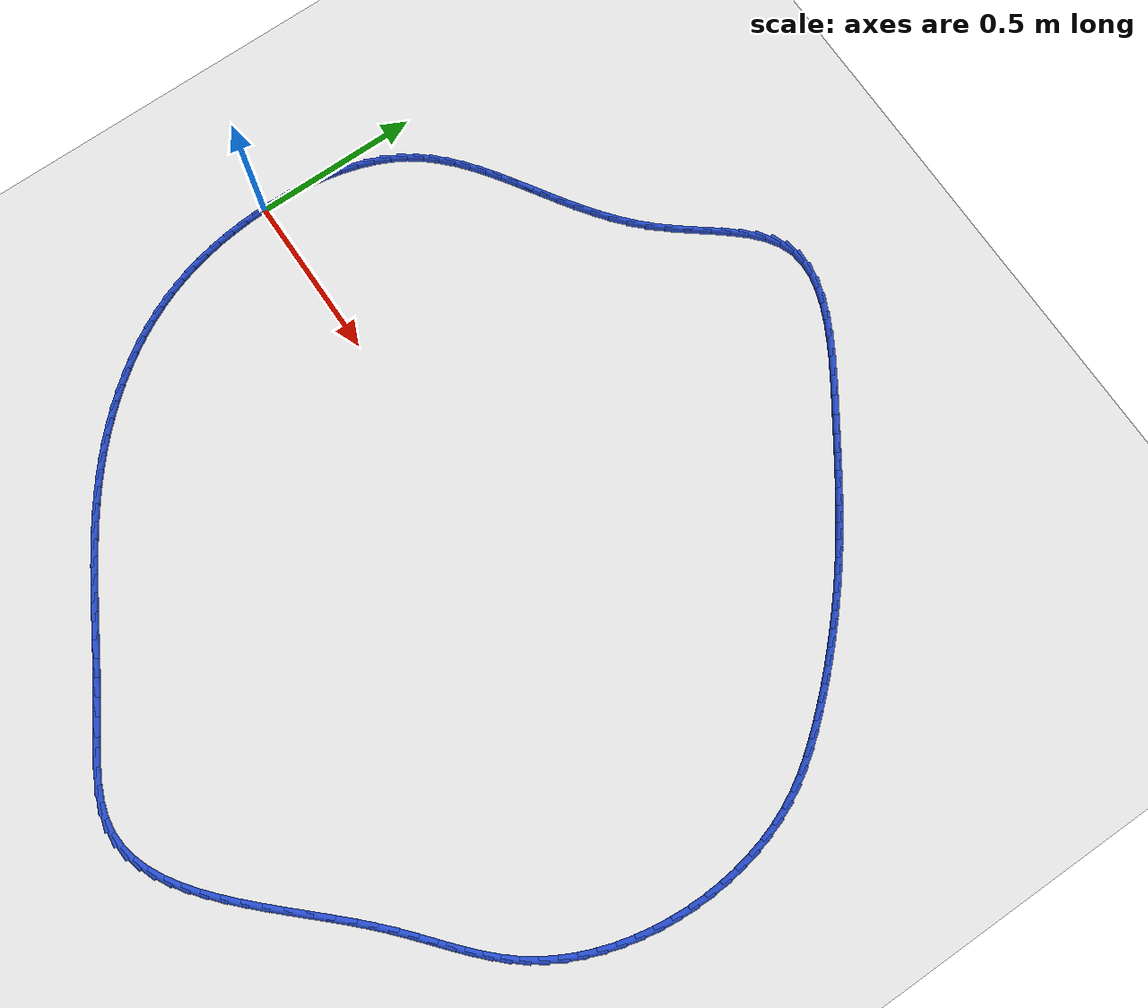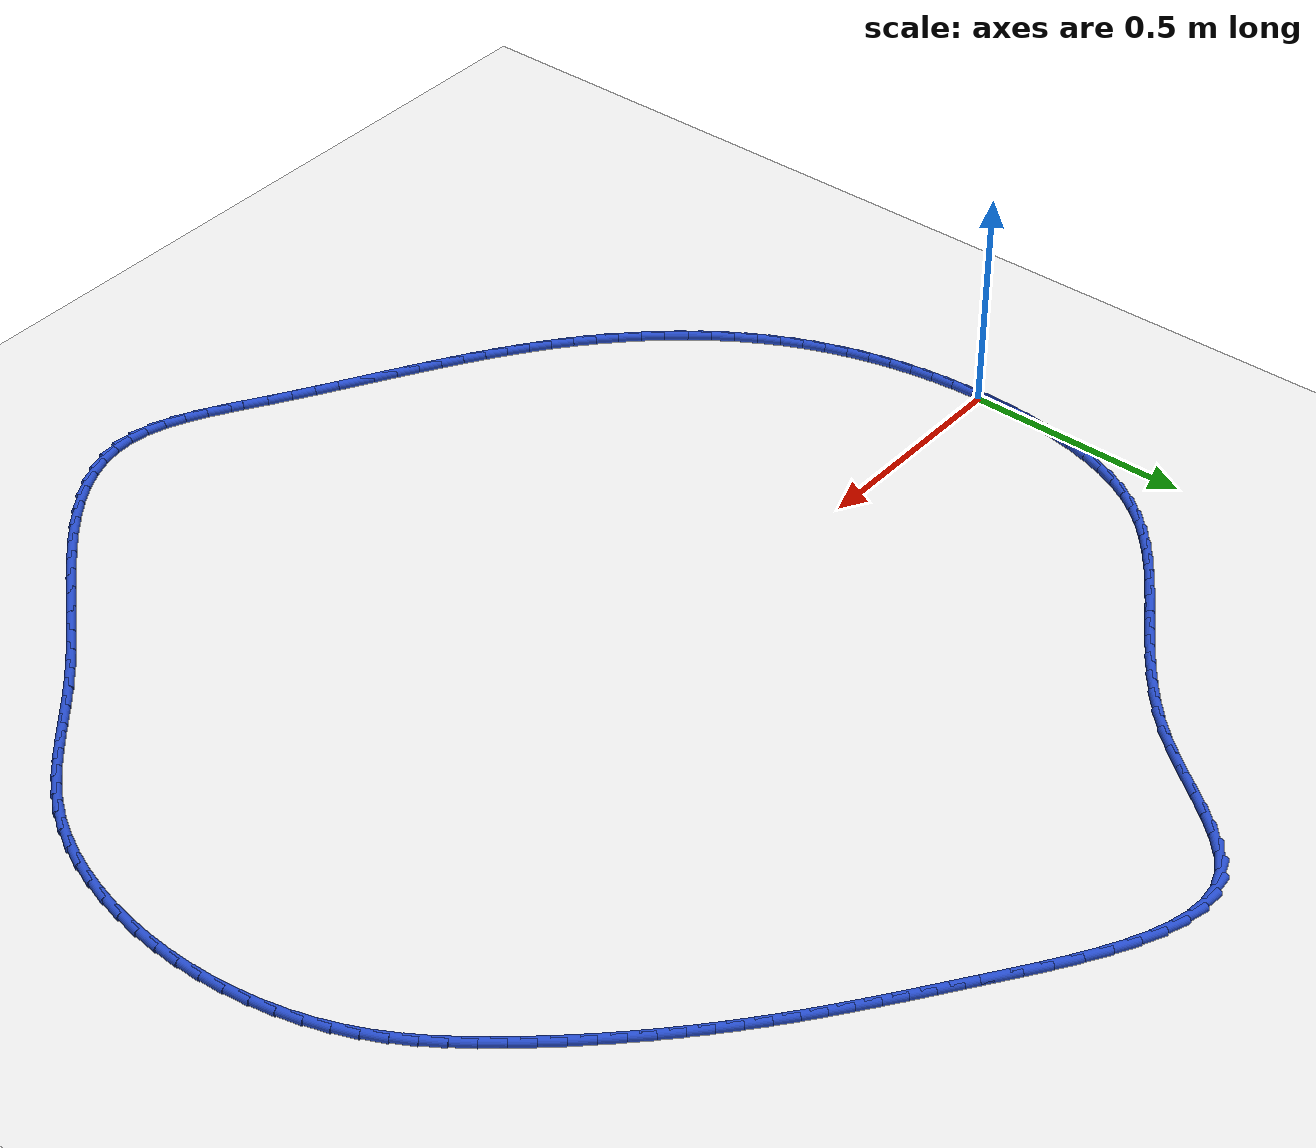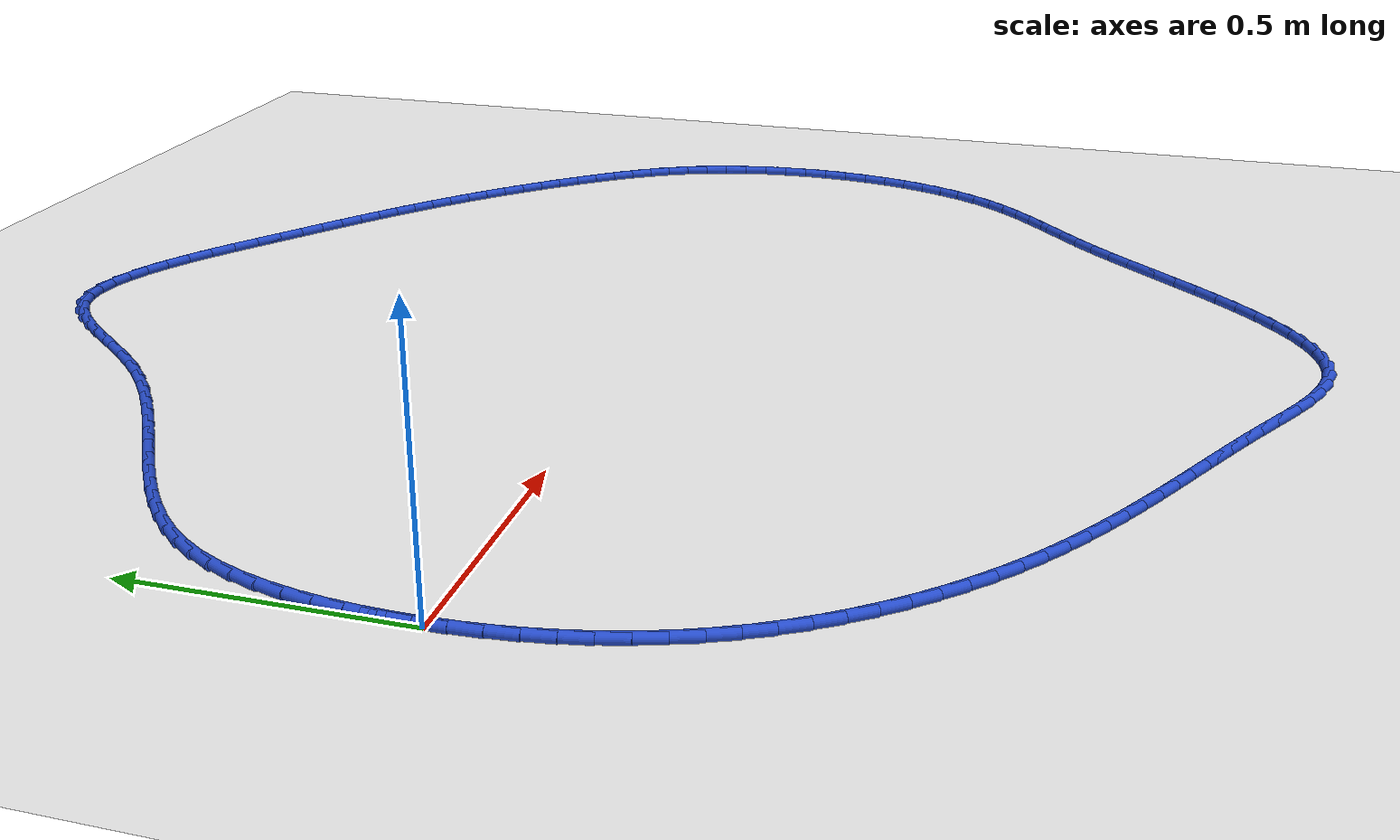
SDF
<sdf version="1.6">
 <world name="default">
  <light name="sun" type="directional">
   <pose>0 0 10 0 -0 0</pose>
   <diffuse>0.8 0.8 0.8 1</diffuse>
   <specular>0.2 0.2 0.2 1</specular>
   <attenuation>
    <range>1000</range>
    <constant>0.9</constant>
    <linear>0.01</linear>
    <quadratic>0.001</quadratic>
   </attenuation>
   <direction>-0.5 0.1 -0.9</direction>
  </light>
  <model name="ground_plane">
   <static>1</static>
   <link name="link">
    <collision name="collision">
     <geometry><plane><normal>0 0 1</normal><size>100 100</size></plane></geometry>
     <surface><friction><ode><mu>100</mu><mu2>50</mu2></ode></friction></surface>
    </collision>
    <visual name="visual">
     <cast_shadows>0</cast_shadows>
     <geometry><plane><normal>0 0 1</normal><size>100 100</size></plane></geometry>
     <material>
      <script><uri>file://media/materials/scripts/gazebo.material</uri><name>Gazebo/WhiteGlow</name></script>
     </material>
    </visual>
   </link>
  </model>
  <gravity>0 0 -9.8</gravity>
  <magnetic_field>6e-06 2.3e-05 -4.2e-05</magnetic_field>
  <atmosphere type="adiabatic"/>
  <physics name="default_physics" default="0" type="ode">
   <max_step_size>0.001</max_step_size>
   <real_time_factor>1</real_time_factor>
   <real_time_update_rate>1000</real_time_update_rate>
  </physics>
  <scene><ambient>0.4 0.4 0.4 1</ambient><background>0.7 0.7 0.7 1</background><shadows>1</shadows></scene>
  <spherical_coordinates>
   <surface_model>EARTH_WGS84</surface_model>
   <latitude_deg>0</latitude_deg>
   <longitude_deg>0</longitude_deg>
   <elevation>0</elevation>
   <heading_deg>0</heading_deg>
  </spherical_coordinates>
  <model name="line">
   <link name="link_0">
    <pose>-1.214306433183765e-17 4.163336342344337e-17 0.01 0 1.57 1.5653247132548307</pose>
    <collision name="collision">
     <geometry><cylinder><radius>0.01</radius><length>0.08</length></cylinder></geometry>
    </collision>
    <visual name="visual">
     <material>
      <script><name>Gazebo/Blue</name><uri>file://media/materials/scripts/gazebo.material</uri></script>
     </material>
     <geometry><cylinder><radius>0.01</radius><length>0.08</length></cylinder></geometry>
    </visual>
   </link>
   <link name="link_1">
    <pose>0.0002891131561396566 0.05283821103352478 0.01 0 1.57 1.5201435535171275</pose>
    <collision name="collision">
     <geometry><cylinder><radius>0.01</radius><length>0.08</length></cylinder></geometry>
    </collision>
    <visual name="visual">
     <material>
      <script><name>Gazebo/Blue</name><uri>file://media/materials/scripts/gazebo.material</uri></script>
     </material>
     <geometry><cylinder><radius>0.01</radius><length>0.08</length></cylinder></geometry>
    </visual>
   </link>
   <link name="link_2">
    <pose>0.0029742547965490684 0.10580361940493893 0.01 0 1.57 1.4710764609372857</pose>
    <collision name="collision">
     <geometry><cylinder><radius>0.01</radius><length>0.08</length></cylinder></geometry>
    </collision>
    <visual name="visual">
     <material>
      <script><name>Gazebo/Blue</name><uri>file://media/materials/scripts/gazebo.material</uri></script>
     </material>
     <geometry><cylinder><radius>0.01</radius><length>0.08</length></cylinder></geometry>
    </visual>
   </link>
   <link name="link_3">
    <pose>0.008241024808958351 0.15844409084244765 0.01 0 1.57 1.4171109490008953</pose>
    <collision name="collision">
     <geometry><cylinder><radius>0.01</radius><length>0.08</length></cylinder></geometry>
    </collision>
    <visual name="visual">
     <material>
      <script><name>Gazebo/Blue</name><uri>file://media/materials/scripts/gazebo.material</uri></script>
     </material>
     <geometry><cylinder><radius>0.01</radius><length>0.08</length></cylinder></geometry>
    </visual>
   </link>
   <link name="link_4">
    <pose>0.01627502308109761 0.21030749107425578 0.01 0 1.57 1.3571242927483247</pose>
    <collision name="collision">
     <geometry><cylinder><radius>0.01</radius><length>0.08</length></cylinder></geometry>
    </collision>
    <visual name="visual">
     <material>
      <script><name>Gazebo/Blue</name><uri>file://media/materials/scripts/gazebo.material</uri></script>
     </material>
     <geometry><cylinder><radius>0.01</radius><length>0.08</length></cylinder></geometry>
    </visual>
   </link>
   <link name="link_5">
    <pose>0.02726184950069699 0.2609416858285687 0.01 0 1.57 1.2898786702113598</pose>
    <collision name="collision">
     <geometry><cylinder><radius>0.01</radius><length>0.08</length></cylinder></geometry>
    </collision>
    <visual name="visual">
     <material>
      <script><name>Gazebo/Blue</name><uri>file://media/materials/scripts/gazebo.material</uri></script>
     </material>
     <geometry><cylinder><radius>0.01</radius><length>0.08</length></cylinder></geometry>
    </visual>
   </link>
   <link name="link_6">
    <pose>0.0413871039554866 0.30989454083359136 0.01 0 1.57 1.2140492613324576</pose>
    <collision name="collision">
     <geometry><cylinder><radius>0.01</radius><length>0.08</length></cylinder></geometry>
    </collision>
    <visual name="visual">
     <material>
      <script><name>Gazebo/Blue</name><uri>file://media/materials/scripts/gazebo.material</uri></script>
     </material>
     <geometry><cylinder><radius>0.01</radius><length>0.08</length></cylinder></geometry>
    </visual>
   </link>
   <link name="link_7">
    <pose>0.05883638633319655 0.3567139218175287 0.01 0 1.57 1.128310022862588</pose>
    <collision name="collision">
     <geometry><cylinder><radius>0.01</radius><length>0.08</length></cylinder></geometry>
    </collision>
    <visual name="visual">
     <material>
      <script><name>Gazebo/Blue</name><uri>file://media/materials/scripts/gazebo.material</uri></script>
     </material>
     <geometry><cylinder><radius>0.01</radius><length>0.08</length></cylinder></geometry>
    </visual>
   </link>
   <link name="link_8">
    <pose>0.07979529652155697 0.4009476945085859 0.01 0 1.57 1.031540856147317</pose>
    <collision name="collision">
     <geometry><cylinder><radius>0.01</radius><length>0.08</length></cylinder></geometry>
    </collision>
    <visual name="visual">
     <material>
      <script><name>Gazebo/Blue</name><uri>file://media/materials/scripts/gazebo.material</uri></script>
     </material>
     <geometry><cylinder><radius>0.01</radius><length>0.08</length></cylinder></geometry>
    </visual>
   </link>
   <link name="link_9">
    <pose>0.10444855251121105 0.44214507661594993 0.01 0 1.57 0.9292899022352308</pose>
    <collision name="collision">
     <geometry><cylinder><radius>0.01</radius><length>0.08</length></cylinder></geometry>
    </collision>
    <visual name="visual">
     <material>
      <script><name>Gazebo/Blue</name><uri>file://media/materials/scripts/gazebo.material</uri></script>
     </material>
     <geometry><cylinder><radius>0.01</radius><length>0.08</length></cylinder></geometry>
    </visual>
   </link>
   <link name="link_10">
    <pose>0.13280976859073773 0.48011759417763555 0.01 0 1.57 0.8365846128096797</pose>
    <collision name="collision">
     <geometry><cylinder><radius>0.01</radius><length>0.08</length></cylinder></geometry>
    </collision>
    <visual name="visual">
     <material>
      <script><name>Gazebo/Blue</name><uri>file://media/materials/scripts/gazebo.material</uri></script>
     </material>
     <geometry><cylinder><radius>0.01</radius><length>0.08</length></cylinder></geometry>
    </visual>
   </link>
   <link name="link_11">
    <pose>0.16451831288126137 0.5152505065031848 0.01 0 1.57 0.7573447239296612</pose>
    <collision name="collision">
     <geometry><cylinder><radius>0.01</radius><length>0.08</length></cylinder></geometry>
    </collision>
    <visual name="visual">
     <material>
      <script><name>Gazebo/Blue</name><uri>file://media/materials/scripts/gazebo.material</uri></script>
     </material>
     <geometry><cylinder><radius>0.01</radius><length>0.08</length></cylinder></geometry>
    </visual>
   </link>
   <link name="link_12">
    <pose>0.19916405919699562 0.5480049495124961 0.01 0 1.57 0.6925076252023527</pose>
    <collision name="collision">
     <geometry><cylinder><radius>0.01</radius><length>0.08</length></cylinder></geometry>
    </collision>
    <visual name="visual">
     <material>
      <script><name>Gazebo/Blue</name><uri>file://media/materials/scripts/gazebo.material</uri></script>
     </material>
     <geometry><cylinder><radius>0.01</radius><length>0.08</length></cylinder></geometry>
    </visual>
   </link>
   <link name="link_13">
    <pose>0.23633688135215453 0.5788420591254685 0.01 0 1.57 0.6420919604782326</pose>
    <collision name="collision">
     <geometry><cylinder><radius>0.01</radius><length>0.08</length></cylinder></geometry>
    </collision>
    <visual name="visual">
     <material>
      <script><name>Gazebo/Blue</name><uri>file://media/materials/scripts/gazebo.material</uri></script>
     </material>
     <geometry><cylinder><radius>0.01</radius><length>0.08</length></cylinder></geometry>
    </visual>
   </link>
   <link name="link_14">
    <pose>0.2756266531609518 0.6082229712620002 0.01 0 1.57 0.6056038954265704</pose>
    <collision name="collision">
     <geometry><cylinder><radius>0.01</radius><length>0.08</length></cylinder></geometry>
    </collision>
    <visual name="visual">
     <material>
      <script><name>Gazebo/Blue</name><uri>file://media/materials/scripts/gazebo.material</uri></script>
     </material>
     <geometry><cylinder><radius>0.01</radius><length>0.08</length></cylinder></geometry>
    </visual>
   </link>
   <link name="link_15">
    <pose>0.3166232484376014 0.6366088218419901 0.01 0 1.57 0.5823569781162897</pose>
    <collision name="collision">
     <geometry><cylinder><radius>0.01</radius><length>0.08</length></cylinder></geometry>
    </collision>
    <visual name="visual">
     <material>
      <script><name>Gazebo/Blue</name><uri>file://media/materials/scripts/gazebo.material</uri></script>
     </material>
     <geometry><cylinder><radius>0.01</radius><length>0.08</length></cylinder></geometry>
    </visual>
   </link>
   <link name="link_16">
    <pose>0.3589165409963174 0.664460746785337 0.01 0 1.57 0.5716758180571649</pose>
    <collision name="collision">
     <geometry><cylinder><radius>0.01</radius><length>0.08</length></cylinder></geometry>
    </collision>
    <visual name="visual">
     <material>
      <script><name>Gazebo/Blue</name><uri>file://media/materials/scripts/gazebo.material</uri></script>
     </material>
     <geometry><cylinder><radius>0.01</radius><length>0.08</length></cylinder></geometry>
    </visual>
   </link>
   <link name="link_17">
    <pose>0.40209640465131335 0.6922398820119394 0.01 0 1.57 0.5730004482977421</pose>
    <collision name="collision">
     <geometry><cylinder><radius>0.01</radius><length>0.08</length></cylinder></geometry>
    </collision>
    <visual name="visual">
     <material>
      <script><name>Gazebo/Blue</name><uri>file://media/materials/scripts/gazebo.material</uri></script>
     </material>
     <geometry><cylinder><radius>0.01</radius><length>0.08</length></cylinder></geometry>
    </visual>
   </link>
   <link name="link_18">
    <pose>0.44575271321680315 0.720407363441696 0.01 0 1.57 0.5859182505860807</pose>
    <collision name="collision">
     <geometry><cylinder><radius>0.01</radius><length>0.08</length></cylinder></geometry>
    </collision>
    <visual name="visual">
     <material>
      <script><name>Gazebo/Blue</name><uri>file://media/materials/scripts/gazebo.material</uri></script>
     </material>
     <geometry><cylinder><radius>0.01</radius><length>0.08</length></cylinder></geometry>
    </visual>
   </link>
   <link name="link_19">
    <pose>0.48947534050700087 0.7494243269945056 0.01 0 1.57 0.6101441137435232</pose>
    <collision name="collision">
     <geometry><cylinder><radius>0.01</radius><length>0.08</length></cylinder></geometry>
    </collision>
    <visual name="visual">
     <material>
      <script><name>Gazebo/Blue</name><uri>file://media/materials/scripts/gazebo.material</uri></script>
     </material>
     <geometry><cylinder><radius>0.01</radius><length>0.08</length></cylinder></geometry>
    </visual>
   </link>
   <link name="link_20">
    <pose>0.5328541603361202 0.7797519085902667 0.01 0 1.57 0.6454602085534941</pose>
    <collision name="collision">
     <geometry><cylinder><radius>0.01</radius><length>0.08</length></cylinder></geometry>
    </collision>
    <visual name="visual">
     <material>
      <script><name>Gazebo/Blue</name><uri>file://media/materials/scripts/gazebo.material</uri></script>
     </material>
     <geometry><cylinder><radius>0.01</radius><length>0.08</length></cylinder></geometry>
    </visual>
   </link>
   <link name="link_21">
    <pose>0.5754790465183752 0.8118512441488782 0.01 0 1.57 0.6916205465917975</pose>
    <collision name="collision">
     <geometry><cylinder><radius>0.01</radius><length>0.08</length></cylinder></geometry>
    </collision>
    <visual name="visual">
     <material>
      <script><name>Gazebo/Blue</name><uri>file://media/materials/scripts/gazebo.material</uri></script>
     </material>
     <geometry><cylinder><radius>0.01</radius><length>0.08</length></cylinder></geometry>
    </visual>
   </link>
   <link name="link_22">
    <pose>0.6169398728679798 0.8461834695902388 0.01 0 1.57 0.7482253124991002</pose>
    <collision name="collision">
     <geometry><cylinder><radius>0.01</radius><length>0.08</length></cylinder></geometry>
    </collision>
    <visual name="visual">
     <material>
      <script><name>Gazebo/Blue</name><uri>file://media/materials/scripts/gazebo.material</uri></script>
     </material>
     <geometry><cylinder><radius>0.01</radius><length>0.08</length></cylinder></geometry>
    </visual>
   </link>
   <link name="link_23">
    <pose>0.6568265131991476 0.8832097208342471 0.01 0 1.57 0.8143756505685936</pose>
    <collision name="collision">
     <geometry><cylinder><radius>0.01</radius><length>0.08</length></cylinder></geometry>
    </collision>
    <visual name="visual">
     <material>
      <script><name>Gazebo/Blue</name><uri>file://media/materials/scripts/gazebo.material</uri></script>
     </material>
     <geometry><cylinder><radius>0.01</radius><length>0.08</length></cylinder></geometry>
    </visual>
   </link>
   <link name="link_24">
    <pose>0.6947340358396832 0.9233803866648422 0.01 0 1.57 0.8749886662335858</pose>
    <collision name="collision">
     <geometry><cylinder><radius>0.01</radius><length>0.08</length></cylinder></geometry>
    </collision>
    <visual name="visual">
     <material>
      <script><name>Gazebo/Blue</name><uri>file://media/materials/scripts/gazebo.material</uri></script>
     </material>
     <geometry><cylinder><radius>0.01</radius><length>0.08</length></cylinder></geometry>
    </visual>
   </link>
   <link name="link_25">
    <pose>0.7306340394677682 0.9663668372345577 0.01 0 1.57 0.9079968809394678</pose>
    <collision name="collision">
     <geometry><cylinder><radius>0.01</radius><length>0.08</length></cylinder></geometry>
    </collision>
    <visual name="visual">
     <material>
      <script><name>Gazebo/Blue</name><uri>file://media/materials/scripts/gazebo.material</uri></script>
     </material>
     <geometry><cylinder><radius>0.01</radius><length>0.08</length></cylinder></geometry>
    </visual>
   </link>
   <link name="link_26">
    <pose>0.7651224515197365 1.010548744073922 0.01 0 1.57 0.9127183252124593</pose>
    <collision name="collision">
     <geometry><cylinder><radius>0.01</radius><length>0.08</length></cylinder></geometry>
    </collision>
    <visual name="visual">
     <material>
      <script><name>Gazebo/Blue</name><uri>file://media/materials/scripts/gazebo.material</uri></script>
     </material>
     <geometry><cylinder><radius>0.01</radius><length>0.08</length></cylinder></geometry>
    </visual>
   </link>
   <link name="link_27">
    <pose>0.7988539617561378 1.0541842030015918 0.01 0 1.57 0.88797338756524</pose>
    <collision name="collision">
     <geometry><cylinder><radius>0.01</radius><length>0.08</length></cylinder></geometry>
    </collision>
    <visual name="visual">
     <material>
      <script><name>Gazebo/Blue</name><uri>file://media/materials/scripts/gazebo.material</uri></script>
     </material>
     <geometry><cylinder><radius>0.01</radius><length>0.08</length></cylinder></geometry>
    </visual>
   </link>
   <link name="link_28">
    <pose>0.8324832599375223 1.095531309836222 0.01 0 1.57 0.8292181348549801</pose>
    <collision name="collision">
     <geometry><cylinder><radius>0.01</radius><length>0.08</length></cylinder></geometry>
    </collision>
    <visual name="visual">
     <material>
      <script><name>Gazebo/Blue</name><uri>file://media/materials/scripts/gazebo.material</uri></script>
     </material>
     <geometry><cylinder><radius>0.01</radius><length>0.08</length></cylinder></geometry>
    </visual>
   </link>
   <link name="link_29">
    <pose>0.8666650358244403 1.1328481603964704 0.01 0 1.57 0.7280273849411397</pose>
    <collision name="collision">
     <geometry><cylinder><radius>0.01</radius><length>0.08</length></cylinder></geometry>
    </collision>
    <visual name="visual">
     <material>
      <script><name>Gazebo/Blue</name><uri>file://media/materials/scripts/gazebo.material</uri></script>
     </material>
     <geometry><cylinder><radius>0.01</radius><length>0.08</length></cylinder></geometry>
    </visual>
   </link>
   <link name="link_30">
    <pose>0.9020539791774416 1.164392850500992 0.01 0 1.57 0.5729254050765923</pose>
    <collision name="collision">
     <geometry><cylinder><radius>0.01</radius><length>0.08</length></cylinder></geometry>
    </collision>
    <visual name="visual">
     <material>
      <script><name>Gazebo/Blue</name><uri>file://media/materials/scripts/gazebo.material</uri></script>
     </material>
     <geometry><cylinder><radius>0.01</radius><length>0.08</length></cylinder></geometry>
    </visual>
   </link>
   <link name="link_31">
    <pose>0.939304779757076 1.1884234759684429 0.01 0 1.57 0.3561416663735436</pose>
    <collision name="collision">
     <geometry><cylinder><radius>0.01</radius><length>0.08</length></cylinder></geometry>
    </collision>
    <visual name="visual">
     <material>
      <script><name>Gazebo/Blue</name><uri>file://media/materials/scripts/gazebo.material</uri></script>
     </material>
     <geometry><cylinder><radius>0.01</radius><length>0.08</length></cylinder></geometry>
    </visual>
   </link>
   <link name="link_32">
    <pose>0.9790656918972335 1.2032147038302263 0.01 0 1.57 0.11469485210553321</pose>
    <collision name="collision">
     <geometry><cylinder><radius>0.01</radius><length>0.08</length></cylinder></geometry>
    </collision>
    <visual name="visual">
     <material>
      <script><name>Gazebo/Blue</name><uri>file://media/materials/scripts/gazebo.material</uri></script>
     </material>
     <geometry><cylinder><radius>0.01</radius><length>0.08</length></cylinder></geometry>
    </visual>
   </link>
   <link name="link_33">
    <pose>1.0215694531640467 1.2081111560908306 0.01 0 1.57 -0.08791245542920716</pose>
    <collision name="collision">
     <geometry><cylinder><radius>0.01</radius><length>0.08</length></cylinder></geometry>
    </collision>
    <visual name="visual">
     <material>
      <script><name>Gazebo/Blue</name><uri>file://media/materials/scripts/gazebo.material</uri></script>
     </material>
     <geometry><cylinder><radius>0.01</radius><length>0.08</length></cylinder></geometry>
    </visual>
   </link>
   <link name="link_34">
    <pose>1.066387256461347 1.2041609311395018 0.01 0 1.57 -0.24368413378447712</pose>
    <collision name="collision">
     <geometry><cylinder><radius>0.01</radius><length>0.08</length></cylinder></geometry>
    </collision>
    <visual name="visual">
     <material>
      <script><name>Gazebo/Blue</name><uri>file://media/materials/scripts/gazebo.material</uri></script>
     </material>
     <geometry><cylinder><radius>0.01</radius><length>0.08</length></cylinder></geometry>
    </visual>
   </link>
   <link name="link_35">
    <pose>1.1130312927364672 1.1925640573035186 0.01 0 1.57 -0.3596852443102934</pose>
    <collision name="collision">
     <geometry><cylinder><radius>0.01</radius><length>0.08</length></cylinder></geometry>
    </collision>
    <visual name="visual">
     <material>
      <script><name>Gazebo/Blue</name><uri>file://media/materials/scripts/gazebo.material</uri></script>
     </material>
     <geometry><cylinder><radius>0.01</radius><length>0.08</length></cylinder></geometry>
    </visual>
   </link>
   <link name="link_36">
    <pose>1.1610137529367413 1.1745205629101596 0.01 0 1.57 -0.44502400251741153</pose>
    <collision name="collision">
     <geometry><cylinder><radius>0.01</radius><length>0.08</length></cylinder></geometry>
    </collision>
    <visual name="visual">
     <material>
      <script><name>Gazebo/Blue</name><uri>file://media/materials/scripts/gazebo.material</uri></script>
     </material>
     <geometry><cylinder><radius>0.01</radius><length>0.08</length></cylinder></geometry>
    </visual>
   </link>
   <link name="link_37">
    <pose>1.209846828009502 1.1512304762867032 0.01 0 1.57 -0.5071855707586936</pose>
    <collision name="collision">
     <geometry><cylinder><radius>0.01</radius><length>0.08</length></cylinder></geometry>
    </collision>
    <visual name="visual">
     <material>
      <script><name>Gazebo/Blue</name><uri>file://media/materials/scripts/gazebo.material</uri></script>
     </material>
     <geometry><cylinder><radius>0.01</radius><length>0.08</length></cylinder></geometry>
    </visual>
   </link>
   <link name="link_38">
    <pose>1.2590427089020826 1.1238938257604276 0.01 0 1.57 -0.55144392417431</pose>
    <collision name="collision">
     <geometry><cylinder><radius>0.01</radius><length>0.08</length></cylinder></geometry>
    </collision>
    <visual name="visual">
     <material>
      <script><name>Gazebo/Blue</name><uri>file://media/materials/scripts/gazebo.material</uri></script>
     </material>
     <geometry><cylinder><radius>0.01</radius><length>0.08</length></cylinder></geometry>
    </visual>
   </link>
   <link name="link_39">
    <pose>1.3081135865618168 1.0937106396586118 0.01 0 1.57 -0.581175812801306</pose>
    <collision name="collision">
     <geometry><cylinder><radius>0.01</radius><length>0.08</length></cylinder></geometry>
    </collision>
    <visual name="visual">
     <material>
      <script><name>Gazebo/Blue</name><uri>file://media/materials/scripts/gazebo.material</uri></script>
     </material>
     <geometry><cylinder><radius>0.01</radius><length>0.08</length></cylinder></geometry>
    </visual>
   </link>
   <link name="link_40">
    <pose>1.3565716519360371 1.0618809463085344 0.01 0 1.57 -0.5982315609858568</pose>
    <collision name="collision">
     <geometry><cylinder><radius>0.01</radius><length>0.08</length></cylinder></geometry>
    </collision>
    <visual name="visual">
     <material>
      <script><name>Gazebo/Blue</name><uri>file://media/materials/scripts/gazebo.material</uri></script>
     </material>
     <geometry><cylinder><radius>0.01</radius><length>0.08</length></cylinder></geometry>
    </visual>
   </link>
   <link name="link_41">
    <pose>1.4039290959720776 1.0296047740374736 0.01 0 1.57 -0.6034413639547701</pose>
    <collision name="collision">
     <geometry><cylinder><radius>0.01</radius><length>0.08</length></cylinder></geometry>
    </collision>
    <visual name="visual">
     <material>
      <script><name>Gazebo/Blue</name><uri>file://media/materials/scripts/gazebo.material</uri></script>
     </material>
     <geometry><cylinder><radius>0.01</radius><length>0.08</length></cylinder></geometry>
    </visual>
   </link>
   <link name="link_42">
    <pose>1.4497129716317485 0.9980504893112909 0.01 0 1.57 -0.6036732991528708</pose>
    <collision name="collision">
     <geometry><cylinder><radius>0.01</radius><length>0.08</length></cylinder></geometry>
    </collision>
    <visual name="visual">
     <material>
      <script><name>Gazebo/Blue</name><uri>file://media/materials/scripts/gazebo.material</uri></script>
     </material>
     <geometry><cylinder><radius>0.01</radius><length>0.08</length></cylinder></geometry>
    </visual>
   </link>
   <link name="link_43">
    <pose>1.4937937129604875 0.9676549235607128 0.01 0 1.57 -0.606281143109904</pose>
    <collision name="collision">
     <geometry><cylinder><radius>0.01</radius><length>0.08</length></cylinder></geometry>
    </collision>
    <visual name="visual">
     <material>
      <script><name>Gazebo/Blue</name><uri>file://media/materials/scripts/gazebo.material</uri></script>
     </material>
     <geometry><cylinder><radius>0.01</radius><length>0.08</length></cylinder></geometry>
    </visual>
   </link>
   <link name="link_44">
    <pose>1.536386001065157 0.9381215283123823 0.01 0 1.57 -0.6118019747373535</pose>
    <collision name="collision">
     <geometry><cylinder><radius>0.01</radius><length>0.08</length></cylinder></geometry>
    </collision>
    <visual name="visual">
     <material>
      <script><name>Gazebo/Blue</name><uri>file://media/materials/scripts/gazebo.material</uri></script>
     </material>
     <geometry><cylinder><radius>0.01</radius><length>0.08</length></cylinder></geometry>
    </visual>
   </link>
   <link name="link_45">
    <pose>1.5777195522630008 0.9091217242570024 0.01 0 1.57 -0.6203454531643335</pose>
    <collision name="collision">
     <geometry><cylinder><radius>0.01</radius><length>0.08</length></cylinder></geometry>
    </collision>
    <visual name="visual">
     <material>
      <script><name>Gazebo/Blue</name><uri>file://media/materials/scripts/gazebo.material</uri></script>
     </material>
     <geometry><cylinder><radius>0.01</radius><length>0.08</length></cylinder></geometry>
    </visual>
   </link>
   <link name="link_46">
    <pose>1.6180240828712615 0.8803269320852743 0.01 0 1.57 -0.6318900314255488</pose>
    <collision name="collision">
     <geometry><cylinder><radius>0.01</radius><length>0.08</length></cylinder></geometry>
    </collision>
    <visual name="visual">
     <material>
      <script><name>Gazebo/Blue</name><uri>file://media/materials/scripts/gazebo.material</uri></script>
     </material>
     <geometry><cylinder><radius>0.01</radius><length>0.08</length></cylinder></geometry>
    </visual>
   </link>
   <link name="link_47">
    <pose>1.6575293092071839 0.8514085724879014 0.01 0 1.57 -0.6462696024870702</pose>
    <collision name="collision">
     <geometry><cylinder><radius>0.01</radius><length>0.08</length></cylinder></geometry>
    </collision>
    <visual name="visual">
     <material>
      <script><name>Gazebo/Blue</name><uri>file://media/materials/scripts/gazebo.material</uri></script>
     </material>
     <geometry><cylinder><radius>0.01</radius><length>0.08</length></cylinder></geometry>
    </visual>
   </link>
   <link name="link_48">
    <pose>1.6964649475880114 0.8220380661555847 0.01 0 1.57 -0.6631754616313987</pose>
    <collision name="collision">
     <geometry><cylinder><radius>0.01</radius><length>0.08</length></cylinder></geometry>
    </collision>
    <visual name="visual">
     <material>
      <script><name>Gazebo/Blue</name><uri>file://media/materials/scripts/gazebo.material</uri></script>
     </material>
     <geometry><cylinder><radius>0.01</radius><length>0.08</length></cylinder></geometry>
    </visual>
   </link>
   <link name="link_49">
    <pose>1.7350607122204624 0.7918868361316789 0.01 0 1.57 -0.6818842022915004</pose>
    <collision name="collision">
     <geometry><cylinder><radius>0.01</radius><length>0.08</length></cylinder></geometry>
    </collision>
    <visual name="visual">
     <material>
      <script><name>Gazebo/Blue</name><uri>file://media/materials/scripts/gazebo.material</uri></script>
     </material>
     <geometry><cylinder><radius>0.01</radius><length>0.08</length></cylinder></geometry>
    </visual>
   </link>
   <link name="link_50">
    <pose>1.7734849497245257 0.7606947133505144 0.01 0 1.57 -0.7010879347161839</pose>
    <collision name="collision">
     <geometry><cylinder><radius>0.01</radius><length>0.08</length></cylinder></geometry>
    </collision>
    <visual name="visual">
     <material>
      <script><name>Gazebo/Blue</name><uri>file://media/materials/scripts/gazebo.material</uri></script>
     </material>
     <geometry><cylinder><radius>0.01</radius><length>0.08</length></cylinder></geometry>
    </visual>
   </link>
   <link name="link_51">
    <pose>1.811684052918641 0.7284489458646023 0.01 0 1.57 -0.7206192090960619</pose>
    <collision name="collision">
     <geometry><cylinder><radius>0.01</radius><length>0.08</length></cylinder></geometry>
    </collision>
    <visual name="visual">
     <material>
      <script><name>Gazebo/Blue</name><uri>file://media/materials/scripts/gazebo.material</uri></script>
     </material>
     <geometry><cylinder><radius>0.01</radius><length>0.08</length></cylinder></geometry>
    </visual>
   </link>
   <link name="link_52">
    <pose>1.8495542517893482 0.6951926994139244 0.01 0 1.57 -0.7405786836207218</pose>
    <collision name="collision">
     <geometry><cylinder><radius>0.01</radius><length>0.08</length></cylinder></geometry>
    </collision>
    <visual name="visual">
     <material>
      <script><name>Gazebo/Blue</name><uri>file://media/materials/scripts/gazebo.material</uri></script>
     </material>
     <geometry><cylinder><radius>0.01</radius><length>0.08</length></cylinder></geometry>
    </visual>
   </link>
   <link name="link_53">
    <pose>1.8869917763231836 0.6609691397384637 0.01 0 1.57 -0.7610670528603201</pose>
    <collision name="collision">
     <geometry><cylinder><radius>0.01</radius><length>0.08</length></cylinder></geometry>
    </collision>
    <visual name="visual">
     <material>
      <script><name>Gazebo/Blue</name><uri>file://media/materials/scripts/gazebo.material</uri></script>
     </material>
     <geometry><cylinder><radius>0.01</radius><length>0.08</length></cylinder></geometry>
    </visual>
   </link>
   <link name="link_54">
    <pose>1.9238928565066888 0.6258214325782036 0.01 0 1.57 -0.7821864114757617</pose>
    <collision name="collision">
     <geometry><cylinder><radius>0.01</radius><length>0.08</length></cylinder></geometry>
    </collision>
    <visual name="visual">
     <material>
      <script><name>Gazebo/Blue</name><uri>file://media/materials/scripts/gazebo.material</uri></script>
     </material>
     <geometry><cylinder><radius>0.01</radius><length>0.08</length></cylinder></geometry>
    </visual>
   </link>
   <link name="link_55">
    <pose>1.9601537223264014 0.5897927436731255 0.01 0 1.57 -0.8040414898198078</pose>
    <collision name="collision">
     <geometry><cylinder><radius>0.01</radius><length>0.08</length></cylinder></geometry>
    </collision>
    <visual name="visual">
     <material>
      <script><name>Gazebo/Blue</name><uri>file://media/materials/scripts/gazebo.material</uri></script>
     </material>
     <geometry><cylinder><radius>0.01</radius><length>0.08</length></cylinder></geometry>
    </visual>
   </link>
   <link name="link_56">
    <pose>1.995670603768862 0.5529262387632137 0.01 0 1.57 -0.8267407818204809</pose>
    <collision name="collision">
     <geometry><cylinder><radius>0.01</radius><length>0.08</length></cylinder></geometry>
    </collision>
    <visual name="visual">
     <material>
      <script><name>Gazebo/Blue</name><uri>file://media/materials/scripts/gazebo.material</uri></script>
     </material>
     <geometry><cylinder><radius>0.01</radius><length>0.08</length></cylinder></geometry>
    </visual>
   </link>
   <link name="link_57">
    <pose>2.0303397308206086 0.5152650835884499 0.01 0 1.57 -0.8503975725137466</pose>
    <collision name="collision">
     <geometry><cylinder><radius>0.01</radius><length>0.08</length></cylinder></geometry>
    </collision>
    <visual name="visual">
     <material>
      <script><name>Gazebo/Blue</name><uri>file://media/materials/scripts/gazebo.material</uri></script>
     </material>
     <geometry><cylinder><radius>0.01</radius><length>0.08</length></cylinder></geometry>
    </visual>
   </link>
   <link name="link_58">
    <pose>2.0640573334681798 0.47685244388881726 0.01 0 1.57 -0.8751656335738047</pose>
    <collision name="collision">
     <geometry><cylinder><radius>0.01</radius><length>0.08</length></cylinder></geometry>
    </collision>
    <visual name="visual">
     <material>
      <script><name>Gazebo/Blue</name><uri>file://media/materials/scripts/gazebo.material</uri></script>
     </material>
     <geometry><cylinder><radius>0.01</radius><length>0.08</length></cylinder></geometry>
    </visual>
   </link>
   <link name="link_59">
    <pose>2.096718423111923 0.43773017969713524 0.01 0 1.57 -0.9045605065855138</pose>
    <collision name="collision">
     <geometry><cylinder><radius>0.01</radius><length>0.08</length></cylinder></geometry>
    </collision>
    <visual name="visual">
     <material>
      <script><name>Gazebo/Blue</name><uri>file://media/materials/scripts/gazebo.material</uri></script>
     </material>
     <geometry><cylinder><radius>0.01</radius><length>0.08</length></cylinder></geometry>
    </visual>
   </link>
   <link name="link_60">
    <pose>2.1280992309088007 0.3978128787897084 0.01 0 1.57 -0.9448733173095397</pose>
    <collision name="collision">
     <geometry><cylinder><radius>0.01</radius><length>0.08</length></cylinder></geometry>
    </collision>
    <visual name="visual">
     <material>
      <script><name>Gazebo/Blue</name><uri>file://media/materials/scripts/gazebo.material</uri></script>
     </material>
     <geometry><cylinder><radius>0.01</radius><length>0.08</length></cylinder></geometry>
    </visual>
   </link>
   <link name="link_61">
    <pose>2.157759305373279 0.3567829549038434 0.01 0 1.57 -0.9967294262238342</pose>
    <collision name="collision">
     <geometry><cylinder><radius>0.01</radius><length>0.08</length></cylinder></geometry>
    </collision>
    <visual name="visual">
     <material>
      <script><name>Gazebo/Blue</name><uri>file://media/materials/scripts/gazebo.material</uri></script>
     </material>
     <geometry><cylinder><radius>0.01</radius><length>0.08</length></cylinder></geometry>
    </visual>
   </link>
   <link name="link_62">
    <pose>2.1852351489913104 0.31429812810752183 0.01 0 1.57 -1.0597891518096259</pose>
    <collision name="collision">
     <geometry><cylinder><radius>0.01</radius><length>0.08</length></cylinder></geometry>
    </collision>
    <visual name="visual">
     <material>
      <script><name>Gazebo/Blue</name><uri>file://media/materials/scripts/gazebo.material</uri></script>
     </material>
     <geometry><cylinder><radius>0.01</radius><length>0.08</length></cylinder></geometry>
    </visual>
   </link>
   <link name="link_63">
    <pose>2.2100632642488467 0.27001611846872436 0.01 0 1.57 -1.133007905849926</pose>
    <collision name="collision">
     <geometry><cylinder><radius>0.01</radius><length>0.08</length></cylinder></geometry>
    </collision>
    <visual name="visual">
     <material>
      <script><name>Gazebo/Blue</name><uri>file://media/materials/scripts/gazebo.material</uri></script>
     </material>
     <geometry><cylinder><radius>0.01</radius><length>0.08</length></cylinder></geometry>
    </visual>
   </link>
   <link name="link_64">
    <pose>2.2317874654202026 0.22360497661044437 0.01 0 1.57 -1.2089745309327193</pose>
    <collision name="collision">
     <geometry><cylinder><radius>0.01</radius><length>0.08</length></cylinder></geometry>
    </collision>
    <visual name="visual">
     <material>
      <script><name>Gazebo/Blue</name><uri>file://media/materials/scripts/gazebo.material</uri></script>
     </material>
     <geometry><cylinder><radius>0.01</radius><length>0.08</length></cylinder></geometry>
    </visual>
   </link>
   <link name="link_65">
    <pose>2.2501687117405567 0.17503954922970455 0.01 0 1.57 -1.2806229291643276</pose>
    <collision name="collision">
     <geometry><cylinder><radius>0.01</radius><length>0.08</length></cylinder></geometry>
    </collision>
    <visual name="visual">
     <material>
      <script><name>Gazebo/Blue</name><uri>file://media/materials/scripts/gazebo.material</uri></script>
     </material>
     <geometry><cylinder><radius>0.01</radius><length>0.08</length></cylinder></geometry>
    </visual>
   </link>
   <link name="link_66">
    <pose>2.2652164000929065 0.12464569137613973 0.01 0 1.57 -1.3482940049164027</pose>
    <collision name="collision">
     <geometry><cylinder><radius>0.01</radius><length>0.08</length></cylinder></geometry>
    </collision>
    <visual name="visual">
     <material>
      <script><name>Gazebo/Blue</name><uri>file://media/materials/scripts/gazebo.material</uri></script>
     </material>
     <geometry><cylinder><radius>0.01</radius><length>0.08</length></cylinder></geometry>
    </visual>
   </link>
   <link name="link_67">
    <pose>2.276953533265975 0.0727684813797472 0.01 0 1.57 -1.4127461443588918</pose>
    <collision name="collision">
     <geometry><cylinder><radius>0.01</radius><length>0.08</length></cylinder></geometry>
    </collision>
    <visual name="visual">
     <material>
      <script><name>Gazebo/Blue</name><uri>file://media/materials/scripts/gazebo.material</uri></script>
     </material>
     <geometry><cylinder><radius>0.01</radius><length>0.08</length></cylinder></geometry>
    </visual>
   </link>
   <link name="link_68">
    <pose>2.285403114048489 0.01975299757052293 0.01 0 1.57 -1.4747324241100883</pose>
    <collision name="collision">
     <geometry><cylinder><radius>0.01</radius><length>0.08</length></cylinder></geometry>
    </collision>
    <visual name="visual">
     <material>
      <script><name>Gazebo/Blue</name><uri>file://media/materials/scripts/gazebo.material</uri></script>
     </material>
     <geometry><cylinder><radius>0.01</radius><length>0.08</length></cylinder></geometry>
    </visual>
   </link>
   <link name="link_69">
    <pose>2.2905881452291728 -0.03405568172153571 0.01 0 1.57 -1.5349915259451106</pose>
    <collision name="collision">
     <geometry><cylinder><radius>0.01</radius><length>0.08</length></cylinder></geometry>
    </collision>
    <visual name="visual">
     <material>
      <script><name>Gazebo/Blue</name><uri>file://media/materials/scripts/gazebo.material</uri></script>
     </material>
     <geometry><cylinder><radius>0.01</radius><length>0.08</length></cylinder></geometry>
    </visual>
   </link>
   <link name="link_70">
    <pose>2.292531629596753 -0.08831247816643287 0.01 0 1.57 1.547344712376488</pose>
    <collision name="collision">
     <geometry><cylinder><radius>0.01</radius><length>0.08</length></cylinder></geometry>
    </collision>
    <visual name="visual">
     <material>
      <script><name>Gazebo/Blue</name><uri>file://media/materials/scripts/gazebo.material</uri></script>
     </material>
     <geometry><cylinder><radius>0.01</radius><length>0.08</length></cylinder></geometry>
    </visual>
   </link>
   <link name="link_71">
    <pose>2.291256569939955 -0.1426723134341711 0.01 0 1.57 1.488374771274081</pose>
    <collision name="collision">
     <geometry><cylinder><radius>0.01</radius><length>0.08</length></cylinder></geometry>
    </collision>
    <visual name="visual">
     <material>
      <script><name>Gazebo/Blue</name><uri>file://media/materials/scripts/gazebo.material</uri></script>
     </material>
     <geometry><cylinder><radius>0.01</radius><length>0.08</length></cylinder></geometry>
    </visual>
   </link>
   <link name="link_72">
    <pose>2.2867859690475045 -0.19679010919475426 0.01 0 1.57 1.4289743394219034</pose>
    <collision name="collision">
     <geometry><cylinder><radius>0.01</radius><length>0.08</length></cylinder></geometry>
    </collision>
    <visual name="visual">
     <material>
      <script><name>Gazebo/Blue</name><uri>file://media/materials/scripts/gazebo.material</uri></script>
     </material>
     <geometry><cylinder><radius>0.01</radius><length>0.08</length></cylinder></geometry>
    </visual>
   </link>
   <link name="link_73">
    <pose>2.279142829708126 -0.25032078711818645 0.01 0 1.57 1.3684155358077381</pose>
    <collision name="collision">
     <geometry><cylinder><radius>0.01</radius><length>0.08</length></cylinder></geometry>
    </collision>
    <visual name="visual">
     <material>
      <script><name>Gazebo/Blue</name><uri>file://media/materials/scripts/gazebo.material</uri></script>
     </material>
     <geometry><cylinder><radius>0.01</radius><length>0.08</length></cylinder></geometry>
    </visual>
   </link>
   <link name="link_74">
    <pose>2.268350154710547 -0.30291926887446946 0.01 0 1.57 1.3059500956653918</pose>
    <collision name="collision">
     <geometry><cylinder><radius>0.01</radius><length>0.08</length></cylinder></geometry>
    </collision>
    <visual name="visual">
     <material>
      <script><name>Gazebo/Blue</name><uri>file://media/materials/scripts/gazebo.material</uri></script>
     </material>
     <geometry><cylinder><radius>0.01</radius><length>0.08</length></cylinder></geometry>
    </visual>
   </link>
   <link name="link_75">
    <pose>2.2544309468434904 -0.35424047613360743 0.01 0 1.57 1.240802730282927</pose>
    <collision name="collision">
     <geometry><cylinder><radius>0.01</radius><length>0.08</length></cylinder></geometry>
    </collision>
    <visual name="visual">
     <material>
      <script><name>Gazebo/Blue</name><uri>file://media/materials/scripts/gazebo.material</uri></script>
     </material>
     <geometry><cylinder><radius>0.01</radius><length>0.08</length></cylinder></geometry>
    </visual>
   </link>
   <link name="link_76">
    <pose>2.237408208895684 -0.4039393305656038 0.01 0 1.57 1.172170246252659</pose>
    <collision name="collision">
     <geometry><cylinder><radius>0.01</radius><length>0.08</length></cylinder></geometry>
    </collision>
    <visual name="visual">
     <material>
      <script><name>Gazebo/Blue</name><uri>file://media/materials/scripts/gazebo.material</uri></script>
     </material>
     <geometry><cylinder><radius>0.01</radius><length>0.08</length></cylinder></geometry>
    </visual>
   </link>
   <link name="link_77">
    <pose>2.2173049436558534 -0.45167075384046196 0.01 0 1.57 1.0992306670727405</pose>
    <collision name="collision">
     <geometry><cylinder><radius>0.01</radius><length>0.08</length></cylinder></geometry>
    </collision>
    <visual name="visual">
     <material>
      <script><name>Gazebo/Blue</name><uri>file://media/materials/scripts/gazebo.material</uri></script>
     </material>
     <geometry><cylinder><radius>0.01</radius><length>0.08</length></cylinder></geometry>
    </visual>
   </link>
   <link name="link_78">
    <pose>2.194144153912722 -0.4970896676281859 0.01 0 1.57 1.0211683048369975</pose>
    <collision name="collision">
     <geometry><cylinder><radius>0.01</radius><length>0.08</length></cylinder></geometry>
    </collision>
    <visual name="visual">
     <material>
      <script><name>Gazebo/Blue</name><uri>file://media/materials/scripts/gazebo.material</uri></script>
     </material>
     <geometry><cylinder><radius>0.01</radius><length>0.08</length></cylinder></geometry>
    </visual>
   </link>
   <link name="link_79">
    <pose>2.167948842455017 -0.5398509935987776 0.01 0 1.57 0.9375025532515058</pose>
    <collision name="collision">
     <geometry><cylinder><radius>0.01</radius><length>0.08</length></cylinder></geometry>
    </collision>
    <visual name="visual">
     <material>
      <script><name>Gazebo/Blue</name><uri>file://media/materials/scripts/gazebo.material</uri></script>
     </material>
     <geometry><cylinder><radius>0.01</radius><length>0.08</length></cylinder></geometry>
    </visual>
   </link>
   <link name="link_80">
    <pose>2.1387476147788984 -0.5796253803741541 0.01 0 1.57 0.8571295840001061</pose>
    <collision name="collision">
     <geometry><cylinder><radius>0.01</radius><length>0.08</length></cylinder></geometry>
    </collision>
    <visual name="visual">
     <material>
      <script><name>Gazebo/Blue</name><uri>file://media/materials/scripts/gazebo.material</uri></script>
     </material>
     <geometry><cylinder><radius>0.01</radius><length>0.08</length></cylinder></geometry>
    </visual>
   </link>
   <link name="link_81">
    <pose>2.1067464695293574 -0.6165814239622107 0.01 0 1.57 0.7927398570487014</pose>
    <collision name="collision">
     <geometry><cylinder><radius>0.01</radius><length>0.08</length></cylinder></geometry>
    </collision>
    <visual name="visual">
     <material>
      <script><name>Gazebo/Blue</name><uri>file://media/materials/scripts/gazebo.material</uri></script>
     </material>
     <geometry><cylinder><radius>0.01</radius><length>0.08</length></cylinder></geometry>
    </visual>
   </link>
   <link name="link_82">
    <pose>2.072360862323251 -0.6514756717787852 0.01 0 1.57 0.7465462474326663</pose>
    <collision name="collision">
     <geometry><cylinder><radius>0.01</radius><length>0.08</length></cylinder></geometry>
    </collision>
    <visual name="visual">
     <material>
      <script><name>Gazebo/Blue</name><uri>file://media/materials/scripts/gazebo.material</uri></script>
     </material>
     <geometry><cylinder><radius>0.01</radius><length>0.08</length></cylinder></geometry>
    </visual>
   </link>
   <link name="link_83">
    <pose>2.036018319795308 -0.6850985549146714 0.01 0 1.57 0.7188896999915876</pose>
    <collision name="collision">
     <geometry><cylinder><radius>0.01</radius><length>0.08</length></cylinder></geometry>
    </collision>
    <visual name="visual">
     <material>
      <script><name>Gazebo/Blue</name><uri>file://media/materials/scripts/gazebo.material</uri></script>
     </material>
     <geometry><cylinder><radius>0.01</radius><length>0.08</length></cylinder></geometry>
    </visual>
   </link>
   <link name="link_84">
    <pose>1.9981463685802545 -0.7182405044606647 0.01 0 1.57 0.709295992482945</pose>
    <collision name="collision">
     <geometry><cylinder><radius>0.01</radius><length>0.08</length></cylinder></geometry>
    </collision>
    <visual name="visual">
     <material>
      <script><name>Gazebo/Blue</name><uri>file://media/materials/scripts/gazebo.material</uri></script>
     </material>
     <geometry><cylinder><radius>0.01</radius><length>0.08</length></cylinder></geometry>
    </visual>
   </link>
   <link name="link_85">
    <pose>1.959172535312819 -0.7516919515075599 0.01 0 1.57 0.716815289029403</pose>
    <collision name="collision">
     <geometry><cylinder><radius>0.01</radius><length>0.08</length></cylinder></geometry>
    </collision>
    <visual name="visual">
     <material>
      <script><name>Gazebo/Blue</name><uri>file://media/materials/scripts/gazebo.material</uri></script>
     </material>
     <geometry><cylinder><radius>0.01</radius><length>0.08</length></cylinder></geometry>
    </visual>
   </link>
   <link name="link_86">
    <pose>1.919524346627728 -0.7862433271461517 0.01 0 1.57 0.7401914751983255</pose>
    <collision name="collision">
     <geometry><cylinder><radius>0.01</radius><length>0.08</length></cylinder></geometry>
    </collision>
    <visual name="visual">
     <material>
      <script><name>Gazebo/Blue</name><uri>file://media/materials/scripts/gazebo.material</uri></script>
     </material>
     <geometry><cylinder><radius>0.01</radius><length>0.08</length></cylinder></geometry>
    </visual>
   </link>
   <link name="link_87">
    <pose>1.8796293285873504 -0.8226850607092993 0.01 0 1.57 0.7734311277408342</pose>
    <collision name="collision">
     <geometry><cylinder><radius>0.01</radius><length>0.08</length></cylinder></geometry>
    </collision>
    <visual name="visual">
     <material>
      <script><name>Gazebo/Blue</name><uri>file://media/materials/scripts/gazebo.material</uri></script>
     </material>
     <geometry><cylinder><radius>0.01</radius><length>0.08</length></cylinder></geometry>
    </visual>
   </link>
   <link name="link_88">
    <pose>1.8398291498522212 -0.8615438794787794 0.01 0 1.57 0.7992972988948601</pose>
    <collision name="collision">
     <geometry><cylinder><radius>0.01</radius><length>0.08</length></cylinder></geometry>
    </collision>
    <visual name="visual">
     <material>
      <script><name>Gazebo/Blue</name><uri>file://media/materials/scripts/gazebo.material</uri></script>
     </material>
     <geometry><cylinder><radius>0.01</radius><length>0.08</length></cylinder></geometry>
    </visual>
   </link>
   <link name="link_89">
    <pose>1.8001412458244523 -0.9023506621147867 0.01 0 1.57 0.8149648660872176</pose>
    <collision name="collision">
     <geometry><cylinder><radius>0.01</radius><length>0.08</length></cylinder></geometry>
    </collision>
    <visual name="visual">
     <material>
      <script><name>Gazebo/Blue</name><uri>file://media/materials/scripts/gazebo.material</uri></script>
     </material>
     <geometry><cylinder><radius>0.01</radius><length>0.08</length></cylinder></geometry>
    </visual>
   </link>
   <link name="link_90">
    <pose>1.760506527272239 -0.9444012498492852 0.01 0 1.57 0.8212526810795969</pose>
    <collision name="collision">
     <geometry><cylinder><radius>0.01</radius><length>0.08</length></cylinder></geometry>
    </collision>
    <visual name="visual">
     <material>
      <script><name>Gazebo/Blue</name><uri>file://media/materials/scripts/gazebo.material</uri></script>
     </material>
     <geometry><cylinder><radius>0.01</radius><length>0.08</length></cylinder></geometry>
    </visual>
   </link>
   <link name="link_91">
    <pose>1.7208659049637767 -0.9869914839142405 0.01 0 1.57 0.8185050450709923</pose>
    <collision name="collision">
     <geometry><cylinder><radius>0.01</radius><length>0.08</length></cylinder></geometry>
    </collision>
    <visual name="visual">
     <material>
      <script><name>Gazebo/Blue</name><uri>file://media/materials/scripts/gazebo.material</uri></script>
     </material>
     <geometry><cylinder><radius>0.01</radius><length>0.08</length></cylinder></geometry>
    </visual>
   </link>
   <link name="link_92">
    <pose>1.681160289667262 -1.0294172055416158 0.01 0 1.57 0.8066189843824776</pose>
    <collision name="collision">
     <geometry><cylinder><radius>0.01</radius><length>0.08</length></cylinder></geometry>
    </collision>
    <visual name="visual">
     <material>
      <script><name>Gazebo/Blue</name><uri>file://media/materials/scripts/gazebo.material</uri></script>
     </material>
     <geometry><cylinder><radius>0.01</radius><length>0.08</length></cylinder></geometry>
    </visual>
   </link>
   <link name="link_93">
    <pose>1.6413305921508894 -1.070974255963376 0.01 0 1.57 0.7850400438844864</pose>
    <collision name="collision">
     <geometry><cylinder><radius>0.01</radius><length>0.08</length></cylinder></geometry>
    </collision>
    <visual name="visual">
     <material>
      <script><name>Gazebo/Blue</name><uri>file://media/materials/scripts/gazebo.material</uri></script>
     </material>
     <geometry><cylinder><radius>0.01</radius><length>0.08</length></cylinder></geometry>
    </visual>
   </link>
   <link name="link_94">
    <pose>1.6013177231828548 -1.1109584764114857 0.01 0 1.57 0.7527286625997496</pose>
    <collision name="collision">
     <geometry><cylinder><radius>0.01</radius><length>0.08</length></cylinder></geometry>
    </collision>
    <visual name="visual">
     <material>
      <script><name>Gazebo/Blue</name><uri>file://media/materials/scripts/gazebo.material</uri></script>
     </material>
     <geometry><cylinder><radius>0.01</radius><length>0.08</length></cylinder></geometry>
    </visual>
   </link>
   <link name="link_95">
    <pose>1.5610625935313522 -1.14866570811791 0.01 0 1.57 0.7081056280828703</pose>
    <collision name="collision">
     <geometry><cylinder><radius>0.01</radius><length>0.08</length></cylinder></geometry>
    </collision>
    <visual name="visual">
     <material>
      <script><name>Gazebo/Blue</name><uri>file://media/materials/scripts/gazebo.material</uri></script>
     </material>
     <geometry><cylinder><radius>0.01</radius><length>0.08</length></cylinder></geometry>
    </visual>
   </link>
   <link name="link_96">
    <pose>1.520506113964579 -1.1833917923146118 0.01 0 1.57 0.649001094173011</pose>
    <collision name="collision">
     <geometry><cylinder><radius>0.01</radius><length>0.08</length></cylinder></geometry>
    </collision>
    <visual name="visual">
     <material>
      <script><name>Gazebo/Blue</name><uri>file://media/materials/scripts/gazebo.material</uri></script>
     </material>
     <geometry><cylinder><radius>0.01</radius><length>0.08</length></cylinder></geometry>
    </visual>
   </link>
   <link name="link_97">
    <pose>1.4795891952507296 -1.2144325702335568 0.01 0 1.57 0.572669501506226</pose>
    <collision name="collision">
     <geometry><cylinder><radius>0.01</radius><length>0.08</length></cylinder></geometry>
    </collision>
    <visual name="visual">
     <material>
      <script><name>Gazebo/Blue</name><uri>file://media/materials/scripts/gazebo.material</uri></script>
     </material>
     <geometry><cylinder><radius>0.01</radius><length>0.08</length></cylinder></geometry>
    </visual>
   </link>
   <link name="link_98">
    <pose>1.4382527481579994 -1.241083883106709 0.01 0 1.57 0.4760088044756101</pose>
    <collision name="collision">
     <geometry><cylinder><radius>0.01</radius><length>0.08</length></cylinder></geometry>
    </collision>
    <visual name="visual">
     <material>
      <script><name>Gazebo/Blue</name><uri>file://media/materials/scripts/gazebo.material</uri></script>
     </material>
     <geometry><cylinder><radius>0.01</radius><length>0.08</length></cylinder></geometry>
    </visual>
   </link>
   <link name="link_99">
    <pose>1.396437683454584 -1.2626415721660331 0.01 0 1.57 0.35623491289577136</pose>
    <collision name="collision">
     <geometry><cylinder><radius>0.01</radius><length>0.08</length></cylinder></geometry>
    </collision>
    <visual name="visual">
     <material>
      <script><name>Gazebo/Blue</name><uri>file://media/materials/scripts/gazebo.material</uri></script>
     </material>
     <geometry><cylinder><radius>0.01</radius><length>0.08</length></cylinder></geometry>
    </visual>
   </link>
   <link name="link_100">
    <pose>1.354084911908678 -1.2784014786434934 0.01 0 1.57 0.21230593463131833</pose>
    <collision name="collision">
     <geometry><cylinder><radius>0.01</radius><length>0.08</length></cylinder></geometry>
    </collision>
    <visual name="visual">
     <material>
      <script><name>Gazebo/Blue</name><uri>file://media/materials/scripts/gazebo.material</uri></script>
     </material>
     <geometry><cylinder><radius>0.01</radius><length>0.08</length></cylinder></geometry>
    </visual>
   </link>
   <link name="link_101">
    <pose>1.3111353442884779 -1.2876594437710545 0.01 0 1.57 0.047020555244151316</pose>
    <collision name="collision">
     <geometry><cylinder><radius>0.01</radius><length>0.08</length></cylinder></geometry>
    </collision>
    <visual name="visual">
     <material>
      <script><name>Gazebo/Blue</name><uri>file://media/materials/scripts/gazebo.material</uri></script>
     </material>
     <geometry><cylinder><radius>0.01</radius><length>0.08</length></cylinder></geometry>
    </visual>
   </link>
   <link name="link_102">
    <pose>1.2675298913621793 -1.289711308780681 0.01 0 1.57 -0.13091471887019346</pose>
    <collision name="collision">
     <geometry><cylinder><radius>0.01</radius><length>0.08</length></cylinder></geometry>
    </collision>
    <visual name="visual">
     <material>
      <script><name>Gazebo/Blue</name><uri>file://media/materials/scripts/gazebo.material</uri></script>
     </material>
     <geometry><cylinder><radius>0.01</radius><length>0.08</length></cylinder></geometry>
    </visual>
   </link>
   <link name="link_103">
    <pose>1.2232117244146907 -1.283876033991782 0.01 0 1.57 -0.2905737713174524</pose>
    <collision name="collision">
     <geometry><cylinder><radius>0.01</radius><length>0.08</length></cylinder></geometry>
    </collision>
    <visual name="visual">
     <material>
      <script><name>Gazebo/Blue</name><uri>file://media/materials/scripts/gazebo.material</uri></script>
     </material>
     <geometry><cylinder><radius>0.01</radius><length>0.08</length></cylinder></geometry>
    </visual>
   </link>
   <link name="link_104">
    <pose>1.178216732093151 -1.2704208323033115 0.01 0 1.57 -0.4056576552784526</pose>
    <collision name="collision">
     <geometry><cylinder><radius>0.01</radius><length>0.08</length></cylinder></geometry>
    </collision>
    <visual name="visual">
     <material>
      <script><name>Gazebo/Blue</name><uri>file://media/materials/scripts/gazebo.material</uri></script>
     </material>
     <geometry><cylinder><radius>0.01</radius><length>0.08</length></cylinder></geometry>
    </visual>
   </link>
   <link name="link_105">
    <pose>1.1327041233461455 -1.2508741560535659 0.01 0 1.57 -0.4824992332986203</pose>
    <collision name="collision">
     <geometry><cylinder><radius>0.01</radius><length>0.08</length></cylinder></geometry>
    </collision>
    <visual name="visual">
     <material>
      <script><name>Gazebo/Blue</name><uri>file://media/materials/scripts/gazebo.material</uri></script>
     </material>
     <geometry><cylinder><radius>0.01</radius><length>0.08</length></cylinder></geometry>
    </visual>
   </link>
   <link name="link_106">
    <pose>1.086841644746767 -1.2268517748240202 0.01 0 1.57 -0.5284465047449839</pose>
    <collision name="collision">
     <geometry><cylinder><radius>0.01</radius><length>0.08</length></cylinder></geometry>
    </collision>
    <visual name="visual">
     <material>
      <script><name>Gazebo/Blue</name><uri>file://media/materials/scripts/gazebo.material</uri></script>
     </material>
     <geometry><cylinder><radius>0.01</radius><length>0.08</length></cylinder></geometry>
    </visual>
   </link>
   <link name="link_107">
    <pose>1.040797042868111 -1.19996945819615 0.01 0 1.57 -0.5482225725851608</pose>
    <collision name="collision">
     <geometry><cylinder><radius>0.01</radius><length>0.08</length></cylinder></geometry>
    </collision>
    <visual name="visual">
     <material>
      <script><name>Gazebo/Blue</name><uri>file://media/materials/scripts/gazebo.material</uri></script>
     </material>
     <geometry><cylinder><radius>0.01</radius><length>0.08</length></cylinder></geometry>
    </visual>
   </link>
   <link name="link_108">
    <pose>0.9947380642832707 -1.17184297575143 0.01 0 1.57 -0.544639673595588</pose>
    <collision name="collision">
     <geometry><cylinder><radius>0.01</radius><length>0.08</length></cylinder></geometry>
    </collision>
    <visual name="visual">
     <material>
      <script><name>Gazebo/Blue</name><uri>file://media/materials/scripts/gazebo.material</uri></script>
     </material>
     <geometry><cylinder><radius>0.01</radius><length>0.08</length></cylinder></geometry>
    </visual>
   </link>
   <link name="link_109">
    <pose>0.9488288367847354 -1.1440332757342941 0.01 0 1.57 -0.532026081633951</pose>
    <collision name="collision">
     <geometry><cylinder><radius>0.01</radius><length>0.08</length></cylinder></geometry>
    </collision>
    <visual name="visual">
     <material>
      <script><name>Gazebo/Blue</name><uri>file://media/materials/scripts/gazebo.material</uri></script>
     </material>
     <geometry><cylinder><radius>0.01</radius><length>0.08</length></cylinder></geometry>
    </visual>
   </link>
   <link name="link_110">
    <pose>0.903171171348249 -1.1171572615335372 0.01 0 1.57 -0.5225130414330025</pose>
    <collision name="collision">
     <geometry><cylinder><radius>0.01</radius><length>0.08</length></cylinder></geometry>
    </collision>
    <visual name="visual">
     <material>
      <script><name>Gazebo/Blue</name><uri>file://media/materials/scripts/gazebo.material</uri></script>
     </material>
     <geometry><cylinder><radius>0.01</radius><length>0.08</length></cylinder></geometry>
    </visual>
   </link>
   <link name="link_111">
    <pose>0.8578143526601623 -1.0910361095435694 0.01 0 1.57 -0.5166461686303685</pose>
    <collision name="collision">
     <geometry><cylinder><radius>0.01</radius><length>0.08</length></cylinder></geometry>
    </collision>
    <visual name="visual">
     <material>
      <script><name>Gazebo/Blue</name><uri>file://media/materials/scripts/gazebo.material</uri></script>
     </material>
     <geometry><cylinder><radius>0.01</radius><length>0.08</length></cylinder></geometry>
    </visual>
   </link>
   <link name="link_112">
    <pose>0.8128060226806153 -1.06546611030441 0.01 0 1.57 -0.5145696283234807</pose>
    <collision name="collision">
     <geometry><cylinder><radius>0.01</radius><length>0.08</length></cylinder></geometry>
    </collision>
    <visual name="visual">
     <material>
      <script><name>Gazebo/Blue</name><uri>file://media/materials/scripts/gazebo.material</uri></script>
     </material>
     <geometry><cylinder><radius>0.01</radius><length>0.08</length></cylinder></geometry>
    </visual>
   </link>
   <link name="link_113">
    <pose>0.7681938233697474 -1.0402435543560797 0.01 0 1.57 -0.5164062735057299</pose>
    <collision name="collision">
     <geometry><cylinder><radius>0.01</radius><length>0.08</length></cylinder></geometry>
    </collision>
    <visual name="visual">
     <material>
      <script><name>Gazebo/Blue</name><uri>file://media/materials/scripts/gazebo.material</uri></script>
     </material>
     <geometry><cylinder><radius>0.01</radius><length>0.08</length></cylinder></geometry>
    </visual>
   </link>
   <link name="link_114">
    <pose>0.7240253966877007 -1.0151647322386006 0.01 0 1.57 -0.5222560073862279</pose>
    <collision name="collision">
     <geometry><cylinder><radius>0.01</radius><length>0.08</length></cylinder></geometry>
    </collision>
    <visual name="visual">
     <material>
      <script><name>Gazebo/Blue</name><uri>file://media/materials/scripts/gazebo.material</uri></script>
     </material>
     <geometry><cylinder><radius>0.01</radius><length>0.08</length></cylinder></geometry>
    </visual>
   </link>
   <link name="link_115">
    <pose>0.6803483845946154 -0.9900259344919929 0.01 0 1.57 -0.5321926380067938</pose>
    <collision name="collision">
     <geometry><cylinder><radius>0.01</radius><length>0.08</length></cylinder></geometry>
    </collision>
    <visual name="visual">
     <material>
      <script><name>Gazebo/Blue</name><uri>file://media/materials/scripts/gazebo.material</uri></script>
     </material>
     <geometry><cylinder><radius>0.01</radius><length>0.08</length></cylinder></geometry>
    </visual>
   </link>
   <link name="link_116">
    <pose>0.6372104290506315 -0.9646234516562776 0.01 0 1.57 -0.5462590167051334</pose>
    <collision name="collision">
     <geometry><cylinder><radius>0.01</radius><length>0.08</length></cylinder></geometry>
    </collision>
    <visual name="visual">
     <material>
      <script><name>Gazebo/Blue</name><uri>file://media/materials/scripts/gazebo.material</uri></script>
     </material>
     <geometry><cylinder><radius>0.01</radius><length>0.08</length></cylinder></geometry>
    </visual>
   </link>
   <link name="link_117">
    <pose>0.5946591720158888 -0.9387535742714745 0.01 0 1.57 -0.5644604287260564</pose>
    <collision name="collision">
     <geometry><cylinder><radius>0.01</radius><length>0.08</length></cylinder></geometry>
    </collision>
    <visual name="visual">
     <material>
      <script><name>Gazebo/Blue</name><uri>file://media/materials/scripts/gazebo.material</uri></script>
     </material>
     <geometry><cylinder><radius>0.01</radius><length>0.08</length></cylinder></geometry>
    </visual>
   </link>
   <link name="link_118">
    <pose>0.5527422554505296 -0.9122125928776061 0.01 0 1.57 -0.586756451067905</pose>
    <collision name="collision">
     <geometry><cylinder><radius>0.01</radius><length>0.08</length></cylinder></geometry>
    </collision>
    <visual name="visual">
     <material>
      <script><name>Gazebo/Blue</name><uri>file://media/materials/scripts/gazebo.material</uri></script>
     </material>
     <geometry><cylinder><radius>0.01</radius><length>0.08</length></cylinder></geometry>
    </visual>
   </link>
   <link name="link_119">
    <pose>0.5115073213146929 -0.8847967980146922 0.01 0 1.57 -0.6130518141425226</pose>
    <collision name="collision">
     <geometry><cylinder><radius>0.01</radius><length>0.08</length></cylinder></geometry>
    </collision>
    <visual name="visual">
     <material>
      <script><name>Gazebo/Blue</name><uri>file://media/materials/scripts/gazebo.material</uri></script>
     </material>
     <geometry><cylinder><radius>0.01</radius><length>0.08</length></cylinder></geometry>
    </visual>
   </link>
   <link name="link_120">
    <pose>0.4710020115685199 -0.8563024802227543 0.01 0 1.57 -0.6431871831965266</pose>
    <collision name="collision">
     <geometry><cylinder><radius>0.01</radius><length>0.08</length></cylinder></geometry>
    </collision>
    <visual name="visual">
     <material>
      <script><name>Gazebo/Blue</name><uri>file://media/materials/scripts/gazebo.material</uri></script>
     </material>
     <geometry><cylinder><radius>0.01</radius><length>0.08</length></cylinder></geometry>
    </visual>
   </link>
   <link name="link_121">
    <pose>0.43127396817215075 -0.8265259300418124 0.01 0 1.57 -0.6769311610373059</pose>
    <collision name="collision">
     <geometry><cylinder><radius>0.01</radius><length>0.08</length></cylinder></geometry>
    </collision>
    <visual name="visual">
     <material>
      <script><name>Gazebo/Blue</name><uri>file://media/materials/scripts/gazebo.material</uri></script>
     </material>
     <geometry><cylinder><radius>0.01</radius><length>0.08</length></cylinder></geometry>
    </visual>
   </link>
   <link name="link_122">
    <pose>0.3923708330857254 -0.7952634380118877 0.01 0 1.57 -0.7139010001355185</pose>
    <collision name="collision">
     <geometry><cylinder><radius>0.01</radius><length>0.08</length></cylinder></geometry>
    </collision>
    <visual name="visual">
     <material>
      <script><name>Gazebo/Blue</name><uri>file://media/materials/scripts/gazebo.material</uri></script>
     </material>
     <geometry><cylinder><radius>0.01</radius><length>0.08</length></cylinder></geometry>
    </visual>
   </link>
   <link name="link_123">
    <pose>0.3543454884740919 -0.7623207686495386 0.01 0 1.57 -0.7526993790927952</pose>
    <collision name="collision">
     <geometry><cylinder><radius>0.01</radius><length>0.08</length></cylinder></geometry>
    </collision>
    <visual name="visual">
     <material>
      <script><name>Gazebo/Blue</name><uri>file://media/materials/scripts/gazebo.material</uri></script>
     </material>
     <geometry><cylinder><radius>0.01</radius><length>0.08</length></cylinder></geometry>
    </visual>
   </link>
   <link name="link_124">
    <pose>0.31733380879131545 -0.7276537315639986 0.01 0 1.57 -0.7926073651240686</pose>
    <collision name="collision">
     <geometry><cylinder><radius>0.01</radius><length>0.08</length></cylinder></geometry>
    </collision>
    <visual name="visual">
     <material>
      <script><name>Gazebo/Blue</name><uri>file://media/materials/scripts/gazebo.material</uri></script>
     </material>
     <geometry><cylinder><radius>0.01</radius><length>0.08</length></cylinder></geometry>
    </visual>
   </link>
   <link name="link_125">
    <pose>0.2815379845031122 -0.6913380317452371 0.01 0 1.57 -0.8339252536202822</pose>
    <collision name="collision">
     <geometry><cylinder><radius>0.01</radius><length>0.08</length></cylinder></geometry>
    </collision>
    <visual name="visual">
     <material>
      <script><name>Gazebo/Blue</name><uri>file://media/materials/scripts/gazebo.material</uri></script>
     </material>
     <geometry><cylinder><radius>0.01</radius><length>0.08</length></cylinder></geometry>
    </visual>
   </link>
   <link name="link_126">
    <pose>0.24716205832748453 -0.653452722944519 0.01 0 1.57 -0.8769765358589026</pose>
    <collision name="collision">
     <geometry><cylinder><radius>0.01</radius><length>0.08</length></cylinder></geometry>
    </collision>
    <visual name="visual">
     <material>
      <script><name>Gazebo/Blue</name><uri>file://media/materials/scripts/gazebo.material</uri></script>
     </material>
     <geometry><cylinder><radius>0.01</radius><length>0.08</length></cylinder></geometry>
    </visual>
   </link>
   <link name="link_127">
    <pose>0.21441007298243644 -0.6140768589131108 0.01 0 1.57 -0.9220830777793051</pose>
    <collision name="collision">
     <geometry><cylinder><radius>0.01</radius><length>0.08</length></cylinder></geometry>
    </collision>
    <visual name="visual">
     <material>
      <script><name>Gazebo/Blue</name><uri>file://media/materials/scripts/gazebo.material</uri></script>
     </material>
     <geometry><cylinder><radius>0.01</radius><length>0.08</length></cylinder></geometry>
    </visual>
   </link>
   <link name="link_128">
    <pose>0.18348607118597035 -0.573289493402278 0.01 0 1.57 -0.9695640441239312</pose>
    <collision name="collision">
     <geometry><cylinder><radius>0.01</radius><length>0.08</length></cylinder></geometry>
    </collision>
    <visual name="visual">
     <material>
      <script><name>Gazebo/Blue</name><uri>file://media/materials/scripts/gazebo.material</uri></script>
     </material>
     <geometry><cylinder><radius>0.01</radius><length>0.08</length></cylinder></geometry>
    </visual>
   </link>
   <link name="link_129">
    <pose>0.15459409565608928 -0.5311696801632858 0.01 0 1.57 -1.0197318386779082</pose>
    <collision name="collision">
     <geometry><cylinder><radius>0.01</radius><length>0.08</length></cylinder></geometry>
    </collision>
    <visual name="visual">
     <material>
      <script><name>Gazebo/Blue</name><uri>file://media/materials/scripts/gazebo.material</uri></script>
     </material>
     <geometry><cylinder><radius>0.01</radius><length>0.08</length></cylinder></geometry>
    </visual>
   </link>
   <link name="link_130">
    <pose>0.12793818911079607 -0.48779647294740003 0.01 0 1.57 -1.0728843843180227</pose>
    <collision name="collision">
     <geometry><cylinder><radius>0.01</radius><length>0.08</length></cylinder></geometry>
    </collision>
    <visual name="visual">
     <material>
      <script><name>Gazebo/Blue</name><uri>file://media/materials/scripts/gazebo.material</uri></script>
     </material>
     <geometry><cylinder><radius>0.01</radius><length>0.08</length></cylinder></geometry>
    </visual>
   </link>
   <link name="link_131">
    <pose>0.10372239426809333 -0.4432489255058854 0.01 0 1.57 -1.1289245766619644</pose>
    <collision name="collision">
     <geometry><cylinder><radius>0.01</radius><length>0.08</length></cylinder></geometry>
    </collision>
    <visual name="visual">
     <material>
      <script><name>Gazebo/Blue</name><uri>file://media/materials/scripts/gazebo.material</uri></script>
     </material>
     <geometry><cylinder><radius>0.01</radius><length>0.08</length></cylinder></geometry>
    </visual>
   </link>
   <link name="link_132">
    <pose>0.08212930404230591 -0.39760424407780925 0.01 0 1.57 -1.185156213863412</pose>
    <collision name="collision">
     <geometry><cylinder><radius>0.01</radius><length>0.08</length></cylinder></geometry>
    </collision>
    <visual name="visual">
     <material>
      <script><name>Gazebo/Blue</name><uri>file://media/materials/scripts/gazebo.material</uri></script>
     </material>
     <geometry><cylinder><radius>0.01</radius><length>0.08</length></cylinder></geometry>
    </visual>
   </link>
   <link name="link_133">
    <pose>0.06317932083897779 -0.35092566512665674 0.01 0 1.57 -1.2400943070402501</pose>
    <collision name="collision">
     <geometry><cylinder><radius>0.01</radius><length>0.08</length></cylinder></geometry>
    </collision>
    <visual name="visual">
     <material>
      <script><name>Gazebo/Blue</name><uri>file://media/materials/scripts/gazebo.material</uri></script>
     </material>
     <geometry><cylinder><radius>0.01</radius><length>0.08</length></cylinder></geometry>
    </visual>
   </link>
   <link name="link_134">
    <pose>0.046818694276249795 -0.3032700381959487 0.01 0 1.57 -1.293513576788088</pose>
    <collision name="collision">
     <geometry><cylinder><radius>0.01</radius><length>0.08</length></cylinder></geometry>
    </collision>
    <visual name="visual">
     <material>
      <script><name>Gazebo/Blue</name><uri>file://media/materials/scripts/gazebo.material</uri></script>
     </material>
     <geometry><cylinder><radius>0.01</radius><length>0.08</length></cylinder></geometry>
    </visual>
   </link>
   <link name="link_135">
    <pose>0.03299329177639877 -0.2546941799099515 0.01 0 1.57 -1.3452413406294914</pose>
    <collision name="collision">
     <geometry><cylinder><radius>0.01</radius><length>0.08</length></cylinder></geometry>
    </collision>
    <visual name="visual">
     <material>
      <script><name>Gazebo/Blue</name><uri>file://media/materials/scripts/gazebo.material</uri></script>
     </material>
     <geometry><cylinder><radius>0.01</radius><length>0.08</length></cylinder></geometry>
    </visual>
   </link>
   <link name="link_136">
    <pose>0.021648980761702213 -0.205254906892934 0.01 0 1.57 -1.395150871834482</pose>
    <collision name="collision">
     <geometry><cylinder><radius>0.01</radius><length>0.08</length></cylinder></geometry>
    </collision>
    <visual name="visual">
     <material>
      <script><name>Gazebo/Blue</name><uri>file://media/materials/scripts/gazebo.material</uri></script>
     </material>
     <geometry><cylinder><radius>0.01</radius><length>0.08</length></cylinder></geometry>
    </visual>
   </link>
   <link name="link_137">
    <pose>0.012731628654437 -0.15500903576916283 0.01 0 1.57 -1.4431590240774184</pose>
    <collision name="collision">
     <geometry><cylinder><radius>0.01</radius><length>0.08</length></cylinder></geometry>
    </collision>
    <visual name="visual">
     <material>
      <script><name>Gazebo/Blue</name><uri>file://media/materials/scripts/gazebo.material</uri></script>
     </material>
     <geometry><cylinder><radius>0.01</radius><length>0.08</length></cylinder></geometry>
    </visual>
   </link>
   <link name="link_138">
    <pose>0.006187102876880171 -0.10401338316290534 0.01 0 1.57 -1.4892221873258726</pose>
    <collision name="collision">
     <geometry><cylinder><radius>0.01</radius><length>0.08</length></cylinder></geometry>
    </collision>
    <visual name="visual">
     <material>
      <script><name>Gazebo/Blue</name><uri>file://media/materials/scripts/gazebo.material</uri></script>
     </material>
     <geometry><cylinder><radius>0.01</radius><length>0.08</length></cylinder></geometry>
    </visual>
   </link>
   <link name="link_139">
    <pose>0.0019612708513088066 -0.05232476569842882 0.01 0 1.57 -1.5333312162789081</pose>
    <collision name="collision">
     <geometry><cylinder><radius>0.01</radius><length>0.08</length></cylinder></geometry>
    </collision>
    <visual name="visual">
     <material>
      <script><name>Gazebo/Blue</name><uri>file://media/materials/scripts/gazebo.material</uri></script>
     </material>
     <geometry><cylinder><radius>0.01</radius><length>0.08</length></cylinder></geometry>
    </visual>
   </link>
   <link name="link_140">
    <pose>-2.42861286636753e-17 1.249000902703301e-16 0.01 0 1.57 1.5660867501119904</pose>
    <collision name="collision">
     <geometry><cylinder><radius>0.01</radius><length>0.08</length></cylinder></geometry>
    </collision>
    <visual name="visual">
     <material>
      <script><name>Gazebo/Blue</name><uri>file://media/materials/scripts/gazebo.material</uri></script>
     </material>
     <geometry><cylinder><radius>0.01</radius><length>0.08</length></cylinder></geometry>
    </visual>
   </link>
   <link name="link_141">
    <pose>0.00024915774523079533 0.05290409730811263 0.01 0 1.57 1.5660867501119906</pose>
    <collision name="collision">
     <geometry><cylinder><radius>0.01</radius><length>0.08</length></cylinder></geometry>
    </collision>
    <visual name="visual">
     <material>
      <script><name>Gazebo/Blue</name><uri>file://media/materials/scripts/gazebo.material</uri></script>
     </material>
     <geometry><cylinder><radius>0.01</radius><length>0.08</length></cylinder></geometry>
    </visual>
   </link>
  </model>
 </world>
</sdf>
